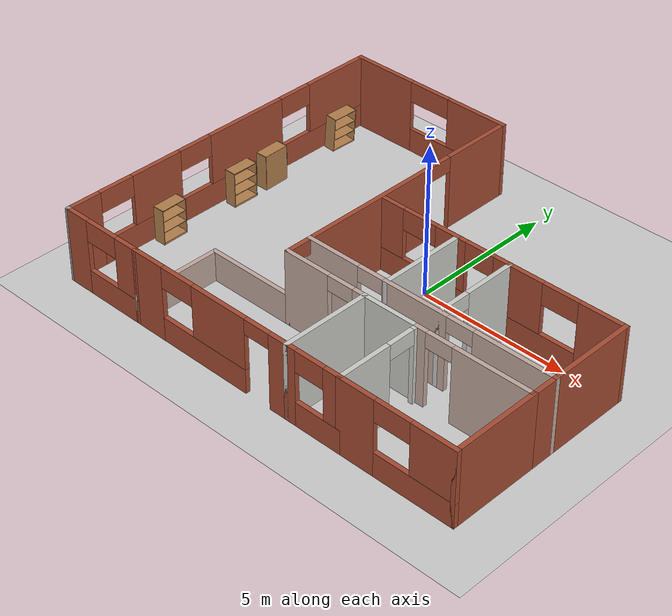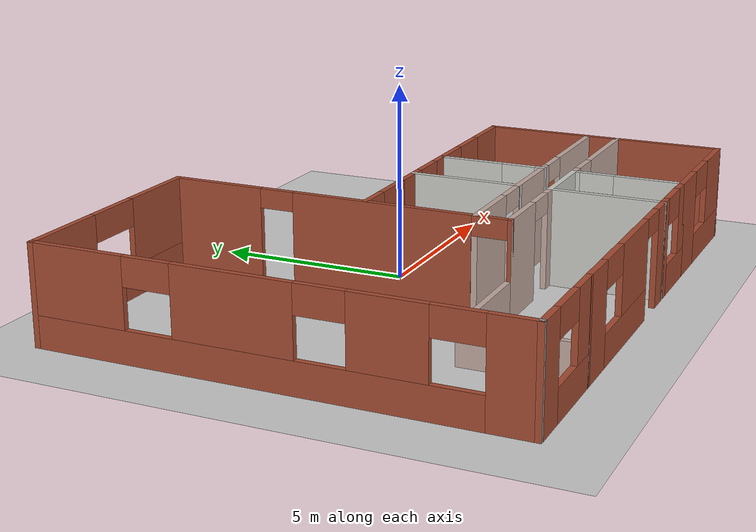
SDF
<sdf version="1.6">
 <world name="default">
  <plugin name="welcome" filename="libwelcome.so"/>
  <light name="sun" type="directional">
   <pose>0 0 10 0 -0 0</pose>
   <diffuse>0.8 0.8 0.8 1</diffuse>
   <specular>0.2 0.2 0.2 1</specular>
   <attenuation>
    <range>1000</range>
    <constant>0.9</constant>
    <linear>0.01</linear>
    <quadratic>0.001</quadratic>
   </attenuation>
   <direction>-0.5 0.1 -0.9</direction>
  </light>
  <model name="ground_plane">
   <static>1</static>
   <link name="link">
    <collision name="collision">
     <geometry><plane><normal>0 0 1</normal><size>100 100</size></plane></geometry>
     <surface><friction><ode><mu>100</mu><mu2>50</mu2></ode></friction></surface>
    </collision>
    <visual name="visual">
     <cast_shadows>0</cast_shadows>
     <geometry><plane><normal>0 0 1</normal><size>100 100</size></plane></geometry>
     <material>
      <script><uri>file://media/materials/scripts/gazebo.material</uri><name>Gazebo/Grey</name></script>
     </material>
    </visual>
   </link>
  </model>
  <gravity>0 0 -9.8</gravity>
  <magnetic_field>6e-06 2.3e-05 -4.2e-05</magnetic_field>
  <atmosphere type="adiabatic"/>
  <physics name="default_physics" default="0" type="ode">
   <max_step_size>0.001</max_step_size>
   <real_time_factor>1</real_time_factor>
   <real_time_update_rate>1000</real_time_update_rate>
  </physics>
  <scene><ambient>0.4 0.4 0.4 1</ambient><background>0.7 0.7 0.7 1</background><shadows>1</shadows></scene>
  <spherical_coordinates>
   <surface_model>EARTH_WGS84</surface_model>
   <latitude_deg>0</latitude_deg>
   <longitude_deg>0</longitude_deg>
   <elevation>0</elevation>
   <heading_deg>0</heading_deg>
  </spherical_coordinates>
  <model name="robot">
   <link name="link_0">
    <pose>0 0 -1e-05 0 -0 0</pose>
    <inertial>
     <mass>1</mass>
     <inertia>
      <ixx>0.166667</ixx>
      <ixy>0</ixy>
      <ixz>0</ixz>
      <iyy>0.166667</iyy>
      <iyz>0</iyz>
      <izz>0.166667</izz>
     </inertia>
    </inertial>
    <visual name="visual">
     <geometry><box><size>0.3 0.3 0.03</size></box></geometry>
     <material>
      <lighting>1</lighting>
      <script><uri>file://media/materials/scripts/gazebo.material</uri><name>Gazebo/Grey</name></script>
      <ambient>0.3 0.3 0.3 1</ambient>
      <diffuse>0.7 0.7 0.7 1</diffuse>
      <specular>0.01 0.01 0.01 1</specular>
      <emissive>0 0 0 1</emissive>
      <shader type="vertex"><normal_map>__default__</normal_map></shader>
     </material>
    </visual>
    <collision name="collision">
     <geometry><box><size>0.3 0.3 0.03</size></box></geometry>
     <surface>
      <friction>
       <ode><mu>1</mu><mu2>1</mu2><fdir1>0 0 0</fdir1><slip1>0</slip1><slip2>0</slip2></ode>
       <torsional>
        <coefficient>1</coefficient>
        <patch_radius>0</patch_radius>
        <surface_radius>0</surface_radius>
        <use_patch_radius>1</use_patch_radius>
        <ode><slip>0</slip></ode>
       </torsional>
      </friction>
      <bounce><restitution_coefficient>0</restitution_coefficient><threshold>1e+06</threshold></bounce>
      <contact>
       <collide_without_contact>0</collide_without_contact>
       <collide_without_contact_bitmask>1</collide_without_contact_bitmask>
       <collide_bitmask>1</collide_bitmask>
       <ode>
        <soft_cfm>0</soft_cfm>
        <soft_erp>0.2</soft_erp>
        <kp>1e+13</kp>
        <kd>1</kd>
        <max_vel>0.01</max_vel>
        <min_depth>0</min_depth>
       </ode>
       <bullet>
        <split_impulse>1</split_impulse>
        <split_impulse_penetration_threshold>-0.01</split_impulse_penetration_threshold>
        <soft_cfm>0</soft_cfm>
        <soft_erp>0.2</soft_erp>
        <kp>1e+13</kp>
        <kd>1</kd>
       </bullet>
      </contact>
     </surface>
    </collision>
   </link>
   <link name="link_1">
    <pose>0.09 -0.165006 2e-06 1.5707 -0 0</pose>
    <inertial>
     <mass>1</mass>
     <inertia><ixx>0.145833</ixx><ixy>0</ixy><ixz>0</ixz><iyy>0.145833</iyy><iyz>0</iyz><izz>0.125</izz></inertia>
    </inertial>
    <visual name="visual">
     <geometry><cylinder><radius>0.06</radius><length>0.03</length></cylinder></geometry>
     <material>
      <lighting>1</lighting>
      <script><uri>file://media/materials/scripts/gazebo.material</uri><name>Gazebo/Grey</name></script>
      <ambient>0.3 0.3 0.3 1</ambient>
      <diffuse>0.7 0.7 0.7 1</diffuse>
      <specular>0.01 0.01 0.01 1</specular>
      <emissive>0 0 0 1</emissive>
      <shader type="vertex"><normal_map>__default__</normal_map></shader>
     </material>
    </visual>
    <collision name="collision">
     <geometry><cylinder><radius>0.06</radius><length>0.03</length></cylinder></geometry>
     <surface>
      <friction>
       <ode><mu>1</mu><mu2>1</mu2><fdir1>0 0 0</fdir1><slip1>0</slip1><slip2>0</slip2></ode>
       <torsional>
        <coefficient>1</coefficient>
        <patch_radius>0</patch_radius>
        <surface_radius>0</surface_radius>
        <use_patch_radius>1</use_patch_radius>
        <ode><slip>0</slip></ode>
       </torsional>
      </friction>
      <bounce><restitution_coefficient>0</restitution_coefficient><threshold>1e+06</threshold></bounce>
      <contact>
       <collide_without_contact>0</collide_without_contact>
       <collide_without_contact_bitmask>1</collide_without_contact_bitmask>
       <collide_bitmask>1</collide_bitmask>
       <ode>
        <soft_cfm>0</soft_cfm>
        <soft_erp>0.2</soft_erp>
        <kp>1e+13</kp>
        <kd>1</kd>
        <max_vel>0.01</max_vel>
        <min_depth>0</min_depth>
       </ode>
       <bullet>
        <split_impulse>1</split_impulse>
        <split_impulse_penetration_threshold>-0.01</split_impulse_penetration_threshold>
        <soft_cfm>0</soft_cfm>
        <soft_erp>0.2</soft_erp>
        <kp>1e+13</kp>
        <kd>1</kd>
       </bullet>
      </contact>
     </surface>
    </collision>
   </link>
   <link name="link_1_clone">
    <pose>-0.09 -0.165006 2e-06 1.5707 -0 0</pose>
    <inertial>
     <mass>1</mass>
     <inertia><ixx>0.145833</ixx><ixy>0</ixy><ixz>0</ixz><iyy>0.145833</iyy><iyz>0</iyz><izz>0.125</izz></inertia>
    </inertial>
    <visual name="visual">
     <geometry><cylinder><radius>0.06</radius><length>0.03</length></cylinder></geometry>
     <material>
      <lighting>1</lighting>
      <script><uri>file://media/materials/scripts/gazebo.material</uri><name>Gazebo/Grey</name></script>
      <ambient>0.3 0.3 0.3 1</ambient>
      <diffuse>0.7 0.7 0.7 1</diffuse>
      <specular>0.01 0.01 0.01 1</specular>
      <emissive>0 0 0 1</emissive>
      <shader type="vertex"><normal_map>__default__</normal_map></shader>
     </material>
    </visual>
    <collision name="collision">
     <geometry><cylinder><radius>0.06</radius><length>0.03</length></cylinder></geometry>
     <surface>
      <friction>
       <ode><mu>1</mu><mu2>1</mu2><fdir1>0 0 0</fdir1><slip1>0</slip1><slip2>0</slip2></ode>
       <torsional>
        <coefficient>1</coefficient>
        <patch_radius>0</patch_radius>
        <surface_radius>0</surface_radius>
        <use_patch_radius>1</use_patch_radius>
        <ode><slip>0</slip></ode>
       </torsional>
      </friction>
      <bounce><restitution_coefficient>0</restitution_coefficient><threshold>1e+06</threshold></bounce>
      <contact>
       <collide_without_contact>0</collide_without_contact>
       <collide_without_contact_bitmask>1</collide_without_contact_bitmask>
       <collide_bitmask>1</collide_bitmask>
       <ode>
        <soft_cfm>0</soft_cfm>
        <soft_erp>0.2</soft_erp>
        <kp>1e+13</kp>
        <kd>1</kd>
        <max_vel>0.01</max_vel>
        <min_depth>0</min_depth>
       </ode>
       <bullet>
        <split_impulse>1</split_impulse>
        <split_impulse_penetration_threshold>-0.01</split_impulse_penetration_threshold>
        <soft_cfm>0</soft_cfm>
        <soft_erp>0.2</soft_erp>
        <kp>1e+13</kp>
        <kd>1</kd>
       </bullet>
      </contact>
     </surface>
    </collision>
   </link>
   <link name="link_1_clone_0">
    <pose>0.09 0.165006 2e-06 1.5707 -0 0</pose>
    <inertial>
     <mass>1</mass>
     <inertia><ixx>0.145833</ixx><ixy>0</ixy><ixz>0</ixz><iyy>0.145833</iyy><iyz>0</iyz><izz>0.125</izz></inertia>
    </inertial>
    <visual name="visual">
     <geometry><cylinder><radius>0.06</radius><length>0.03</length></cylinder></geometry>
     <material>
      <lighting>1</lighting>
      <script><uri>file://media/materials/scripts/gazebo.material</uri><name>Gazebo/Grey</name></script>
      <ambient>0.3 0.3 0.3 1</ambient>
      <diffuse>0.7 0.7 0.7 1</diffuse>
      <specular>0.01 0.01 0.01 1</specular>
      <emissive>0 0 0 1</emissive>
      <shader type="vertex"><normal_map>__default__</normal_map></shader>
     </material>
    </visual>
    <collision name="collision">
     <geometry><cylinder><radius>0.06</radius><length>0.03</length></cylinder></geometry>
     <surface>
      <friction>
       <ode><mu>1</mu><mu2>1</mu2><fdir1>0 0 0</fdir1><slip1>0</slip1><slip2>0</slip2></ode>
       <torsional>
        <coefficient>1</coefficient>
        <patch_radius>0</patch_radius>
        <surface_radius>0</surface_radius>
        <use_patch_radius>1</use_patch_radius>
        <ode><slip>0</slip></ode>
       </torsional>
      </friction>
      <bounce><restitution_coefficient>0</restitution_coefficient><threshold>1e+06</threshold></bounce>
      <contact>
       <collide_without_contact>0</collide_without_contact>
       <collide_without_contact_bitmask>1</collide_without_contact_bitmask>
       <collide_bitmask>1</collide_bitmask>
       <ode>
        <soft_cfm>0</soft_cfm>
        <soft_erp>0.2</soft_erp>
        <kp>1e+13</kp>
        <kd>1</kd>
        <max_vel>0.01</max_vel>
        <min_depth>0</min_depth>
       </ode>
       <bullet>
        <split_impulse>1</split_impulse>
        <split_impulse_penetration_threshold>-0.01</split_impulse_penetration_threshold>
        <soft_cfm>0</soft_cfm>
        <soft_erp>0.2</soft_erp>
        <kp>1e+13</kp>
        <kd>1</kd>
       </bullet>
      </contact>
     </surface>
    </collision>
   </link>
   <link name="link_1_clone_1">
    <pose>-0.09 0.165006 2e-06 1.5707 -0 0</pose>
    <inertial>
     <mass>1</mass>
     <inertia><ixx>0.145833</ixx><ixy>0</ixy><ixz>0</ixz><iyy>0.145833</iyy><iyz>0</iyz><izz>0.125</izz></inertia>
    </inertial>
    <visual name="visual">
     <geometry><cylinder><radius>0.06</radius><length>0.03</length></cylinder></geometry>
     <material>
      <lighting>1</lighting>
      <script><uri>file://media/materials/scripts/gazebo.material</uri><name>Gazebo/Grey</name></script>
      <ambient>0.3 0.3 0.3 1</ambient>
      <diffuse>0.7 0.7 0.7 1</diffuse>
      <specular>0.01 0.01 0.01 1</specular>
      <emissive>0 0 0 1</emissive>
      <shader type="vertex"><normal_map>__default__</normal_map></shader>
     </material>
    </visual>
    <collision name="collision">
     <geometry><cylinder><radius>0.06</radius><length>0.03</length></cylinder></geometry>
     <surface>
      <friction>
       <ode><mu>1</mu><mu2>1</mu2><fdir1>0 0 0</fdir1><slip1>0</slip1><slip2>0</slip2></ode>
       <torsional>
        <coefficient>1</coefficient>
        <patch_radius>0</patch_radius>
        <surface_radius>0</surface_radius>
        <use_patch_radius>1</use_patch_radius>
        <ode><slip>0</slip></ode>
       </torsional>
      </friction>
      <bounce><restitution_coefficient>0</restitution_coefficient><threshold>1e+06</threshold></bounce>
      <contact>
       <collide_without_contact>0</collide_without_contact>
       <collide_without_contact_bitmask>1</collide_without_contact_bitmask>
       <collide_bitmask>1</collide_bitmask>
       <ode>
        <soft_cfm>0</soft_cfm>
        <soft_erp>0.2</soft_erp>
        <kp>1e+13</kp>
        <kd>1</kd>
        <max_vel>0.01</max_vel>
        <min_depth>0</min_depth>
       </ode>
       <bullet>
        <split_impulse>1</split_impulse>
        <split_impulse_penetration_threshold>-0.01</split_impulse_penetration_threshold>
        <soft_cfm>0</soft_cfm>
        <soft_erp>0.2</soft_erp>
        <kp>1e+13</kp>
        <kd>1</kd>
       </bullet>
      </contact>
     </surface>
    </collision>
   </link>
   <joint name="link_0_JOINT_0" type="revolute">
    <parent>link_0</parent>
    <child>link_1</child>
    <axis>
     <xyz>0 0 1</xyz>
     <use_parent_model_frame>0</use_parent_model_frame>
     <limit>
      <lower>-1.79769e+308</lower>
      <upper>1.79769e+308</upper>
      <effort>-1</effort>
      <velocity>-1</velocity>
     </limit>
     <dynamics>
      <spring_reference>0</spring_reference>
      <spring_stiffness>0</spring_stiffness>
      <damping>0</damping>
     </dynamics>
    </axis>
    <physics>
     <ode><limit><cfm>0</cfm><erp>0.2</erp></limit><suspension><cfm>0</cfm><erp>0.2</erp></suspension></ode>
    </physics>
   </joint>
   <joint name="link_0_JOINT_1" type="revolute">
    <parent>link_0</parent>
    <child>link_1_clone</child>
    <axis>
     <xyz>0 0 1</xyz>
     <use_parent_model_frame>0</use_parent_model_frame>
     <limit>
      <lower>-1.79769e+308</lower>
      <upper>1.79769e+308</upper>
      <effort>-1</effort>
      <velocity>-1</velocity>
     </limit>
     <dynamics>
      <spring_reference>0</spring_reference>
      <spring_stiffness>0</spring_stiffness>
      <damping>0</damping>
     </dynamics>
    </axis>
    <physics>
     <ode><limit><cfm>0</cfm><erp>0.2</erp></limit><suspension><cfm>0</cfm><erp>0.2</erp></suspension></ode>
    </physics>
   </joint>
   <joint name="link_0_JOINT_2" type="revolute">
    <parent>link_0</parent>
    <child>link_1_clone_0</child>
    <axis>
     <xyz>0 0 1</xyz>
     <use_parent_model_frame>0</use_parent_model_frame>
     <limit>
      <lower>-1.79769e+308</lower>
      <upper>1.79769e+308</upper>
      <effort>-1</effort>
      <velocity>-1</velocity>
     </limit>
     <dynamics>
      <spring_reference>0</spring_reference>
      <spring_stiffness>0</spring_stiffness>
      <damping>0</damping>
     </dynamics>
    </axis>
    <physics>
     <ode><limit><cfm>0</cfm><erp>0.2</erp></limit><suspension><cfm>0</cfm><erp>0.2</erp></suspension></ode>
    </physics>
   </joint>
   <joint name="link_0_JOINT_3" type="revolute">
    <parent>link_0</parent>
    <child>link_1_clone_1</child>
    <axis>
     <xyz>0 0 1</xyz>
     <use_parent_model_frame>0</use_parent_model_frame>
     <limit>
      <lower>-1.79769e+308</lower>
      <upper>1.79769e+308</upper>
      <effort>-1</effort>
      <velocity>-1</velocity>
     </limit>
     <dynamics>
      <spring_reference>0</spring_reference>
      <spring_stiffness>0</spring_stiffness>
      <damping>0</damping>
     </dynamics>
    </axis>
    <physics>
     <ode><limit><cfm>0</cfm><erp>0.2</erp></limit><suspension><cfm>0</cfm><erp>0.2</erp></suspension></ode>
    </physics>
   </joint>
   <static>0</static>
   <pose>-2.65526 -0.348359 0.059998 2e-06 1.5e-05 0.105774</pose>
  </model>
  <model name="robot_0">
   <link name="link_0">
    <pose>0 0 -1e-05 0 -0 0</pose>
    <inertial>
     <mass>1</mass>
     <inertia>
      <ixx>0.166667</ixx>
      <ixy>0</ixy>
      <ixz>0</ixz>
      <iyy>0.166667</iyy>
      <iyz>0</iyz>
      <izz>0.166667</izz>
     </inertia>
    </inertial>
    <visual name="visual">
     <geometry><box><size>0.3 0.3 0.03</size></box></geometry>
     <material>
      <lighting>1</lighting>
      <script><uri>file://media/materials/scripts/gazebo.material</uri><name>Gazebo/Grey</name></script>
      <ambient>0.3 0.3 0.3 1</ambient>
      <diffuse>0.7 0.7 0.7 1</diffuse>
      <specular>0.01 0.01 0.01 1</specular>
      <emissive>0 0 0 1</emissive>
      <shader type="vertex"><normal_map>__default__</normal_map></shader>
     </material>
    </visual>
    <collision name="collision">
     <geometry><box><size>0.3 0.3 0.03</size></box></geometry>
     <surface>
      <friction>
       <ode><mu>1</mu><mu2>1</mu2><fdir1>0 0 0</fdir1><slip1>0</slip1><slip2>0</slip2></ode>
       <torsional>
        <coefficient>1</coefficient>
        <patch_radius>0</patch_radius>
        <surface_radius>0</surface_radius>
        <use_patch_radius>1</use_patch_radius>
        <ode><slip>0</slip></ode>
       </torsional>
      </friction>
      <bounce><restitution_coefficient>0</restitution_coefficient><threshold>1e+06</threshold></bounce>
      <contact>
       <collide_without_contact>0</collide_without_contact>
       <collide_without_contact_bitmask>1</collide_without_contact_bitmask>
       <collide_bitmask>1</collide_bitmask>
       <ode>
        <soft_cfm>0</soft_cfm>
        <soft_erp>0.2</soft_erp>
        <kp>1e+13</kp>
        <kd>1</kd>
        <max_vel>0.01</max_vel>
        <min_depth>0</min_depth>
       </ode>
       <bullet>
        <split_impulse>1</split_impulse>
        <split_impulse_penetration_threshold>-0.01</split_impulse_penetration_threshold>
        <soft_cfm>0</soft_cfm>
        <soft_erp>0.2</soft_erp>
        <kp>1e+13</kp>
        <kd>1</kd>
       </bullet>
      </contact>
     </surface>
    </collision>
   </link>
   <link name="link_1">
    <pose>0.09 -0.165006 2e-06 1.5707 -0 0</pose>
    <inertial>
     <mass>1</mass>
     <inertia><ixx>0.145833</ixx><ixy>0</ixy><ixz>0</ixz><iyy>0.145833</iyy><iyz>0</iyz><izz>0.125</izz></inertia>
    </inertial>
    <visual name="visual">
     <geometry><cylinder><radius>0.06</radius><length>0.03</length></cylinder></geometry>
     <material>
      <lighting>1</lighting>
      <script><uri>file://media/materials/scripts/gazebo.material</uri><name>Gazebo/Grey</name></script>
      <ambient>0.3 0.3 0.3 1</ambient>
      <diffuse>0.7 0.7 0.7 1</diffuse>
      <specular>0.01 0.01 0.01 1</specular>
      <emissive>0 0 0 1</emissive>
      <shader type="vertex"><normal_map>__default__</normal_map></shader>
     </material>
    </visual>
    <collision name="collision">
     <geometry><cylinder><radius>0.06</radius><length>0.03</length></cylinder></geometry>
     <surface>
      <friction>
       <ode><mu>1</mu><mu2>1</mu2><fdir1>0 0 0</fdir1><slip1>0</slip1><slip2>0</slip2></ode>
       <torsional>
        <coefficient>1</coefficient>
        <patch_radius>0</patch_radius>
        <surface_radius>0</surface_radius>
        <use_patch_radius>1</use_patch_radius>
        <ode><slip>0</slip></ode>
       </torsional>
      </friction>
      <bounce><restitution_coefficient>0</restitution_coefficient><threshold>1e+06</threshold></bounce>
      <contact>
       <collide_without_contact>0</collide_without_contact>
       <collide_without_contact_bitmask>1</collide_without_contact_bitmask>
       <collide_bitmask>1</collide_bitmask>
       <ode>
        <soft_cfm>0</soft_cfm>
        <soft_erp>0.2</soft_erp>
        <kp>1e+13</kp>
        <kd>1</kd>
        <max_vel>0.01</max_vel>
        <min_depth>0</min_depth>
       </ode>
       <bullet>
        <split_impulse>1</split_impulse>
        <split_impulse_penetration_threshold>-0.01</split_impulse_penetration_threshold>
        <soft_cfm>0</soft_cfm>
        <soft_erp>0.2</soft_erp>
        <kp>1e+13</kp>
        <kd>1</kd>
       </bullet>
      </contact>
     </surface>
    </collision>
   </link>
   <link name="link_1_clone">
    <pose>-0.09 -0.165006 2e-06 1.5707 -0 0</pose>
    <inertial>
     <mass>1</mass>
     <inertia><ixx>0.145833</ixx><ixy>0</ixy><ixz>0</ixz><iyy>0.145833</iyy><iyz>0</iyz><izz>0.125</izz></inertia>
    </inertial>
    <visual name="visual">
     <geometry><cylinder><radius>0.06</radius><length>0.03</length></cylinder></geometry>
     <material>
      <lighting>1</lighting>
      <script><uri>file://media/materials/scripts/gazebo.material</uri><name>Gazebo/Grey</name></script>
      <ambient>0.3 0.3 0.3 1</ambient>
      <diffuse>0.7 0.7 0.7 1</diffuse>
      <specular>0.01 0.01 0.01 1</specular>
      <emissive>0 0 0 1</emissive>
      <shader type="vertex"><normal_map>__default__</normal_map></shader>
     </material>
    </visual>
    <collision name="collision">
     <geometry><cylinder><radius>0.06</radius><length>0.03</length></cylinder></geometry>
     <surface>
      <friction>
       <ode><mu>1</mu><mu2>1</mu2><fdir1>0 0 0</fdir1><slip1>0</slip1><slip2>0</slip2></ode>
       <torsional>
        <coefficient>1</coefficient>
        <patch_radius>0</patch_radius>
        <surface_radius>0</surface_radius>
        <use_patch_radius>1</use_patch_radius>
        <ode><slip>0</slip></ode>
       </torsional>
      </friction>
      <bounce><restitution_coefficient>0</restitution_coefficient><threshold>1e+06</threshold></bounce>
      <contact>
       <collide_without_contact>0</collide_without_contact>
       <collide_without_contact_bitmask>1</collide_without_contact_bitmask>
       <collide_bitmask>1</collide_bitmask>
       <ode>
        <soft_cfm>0</soft_cfm>
        <soft_erp>0.2</soft_erp>
        <kp>1e+13</kp>
        <kd>1</kd>
        <max_vel>0.01</max_vel>
        <min_depth>0</min_depth>
       </ode>
       <bullet>
        <split_impulse>1</split_impulse>
        <split_impulse_penetration_threshold>-0.01</split_impulse_penetration_threshold>
        <soft_cfm>0</soft_cfm>
        <soft_erp>0.2</soft_erp>
        <kp>1e+13</kp>
        <kd>1</kd>
       </bullet>
      </contact>
     </surface>
    </collision>
   </link>
   <link name="link_1_clone_0">
    <pose>0.09 0.165006 2e-06 1.5707 -0 0</pose>
    <inertial>
     <mass>1</mass>
     <inertia><ixx>0.145833</ixx><ixy>0</ixy><ixz>0</ixz><iyy>0.145833</iyy><iyz>0</iyz><izz>0.125</izz></inertia>
    </inertial>
    <visual name="visual">
     <geometry><cylinder><radius>0.06</radius><length>0.03</length></cylinder></geometry>
     <material>
      <lighting>1</lighting>
      <script><uri>file://media/materials/scripts/gazebo.material</uri><name>Gazebo/Grey</name></script>
      <ambient>0.3 0.3 0.3 1</ambient>
      <diffuse>0.7 0.7 0.7 1</diffuse>
      <specular>0.01 0.01 0.01 1</specular>
      <emissive>0 0 0 1</emissive>
      <shader type="vertex"><normal_map>__default__</normal_map></shader>
     </material>
    </visual>
    <collision name="collision">
     <geometry><cylinder><radius>0.06</radius><length>0.03</length></cylinder></geometry>
     <surface>
      <friction>
       <ode><mu>1</mu><mu2>1</mu2><fdir1>0 0 0</fdir1><slip1>0</slip1><slip2>0</slip2></ode>
       <torsional>
        <coefficient>1</coefficient>
        <patch_radius>0</patch_radius>
        <surface_radius>0</surface_radius>
        <use_patch_radius>1</use_patch_radius>
        <ode><slip>0</slip></ode>
       </torsional>
      </friction>
      <bounce><restitution_coefficient>0</restitution_coefficient><threshold>1e+06</threshold></bounce>
      <contact>
       <collide_without_contact>0</collide_without_contact>
       <collide_without_contact_bitmask>1</collide_without_contact_bitmask>
       <collide_bitmask>1</collide_bitmask>
       <ode>
        <soft_cfm>0</soft_cfm>
        <soft_erp>0.2</soft_erp>
        <kp>1e+13</kp>
        <kd>1</kd>
        <max_vel>0.01</max_vel>
        <min_depth>0</min_depth>
       </ode>
       <bullet>
        <split_impulse>1</split_impulse>
        <split_impulse_penetration_threshold>-0.01</split_impulse_penetration_threshold>
        <soft_cfm>0</soft_cfm>
        <soft_erp>0.2</soft_erp>
        <kp>1e+13</kp>
        <kd>1</kd>
       </bullet>
      </contact>
     </surface>
    </collision>
   </link>
   <link name="link_1_clone_1">
    <pose>-0.09 0.165006 2e-06 1.5707 -0 0</pose>
    <inertial>
     <mass>1</mass>
     <inertia><ixx>0.145833</ixx><ixy>0</ixy><ixz>0</ixz><iyy>0.145833</iyy><iyz>0</iyz><izz>0.125</izz></inertia>
    </inertial>
    <visual name="visual">
     <geometry><cylinder><radius>0.06</radius><length>0.03</length></cylinder></geometry>
     <material>
      <lighting>1</lighting>
      <script><uri>file://media/materials/scripts/gazebo.material</uri><name>Gazebo/Grey</name></script>
      <ambient>0.3 0.3 0.3 1</ambient>
      <diffuse>0.7 0.7 0.7 1</diffuse>
      <specular>0.01 0.01 0.01 1</specular>
      <emissive>0 0 0 1</emissive>
      <shader type="vertex"><normal_map>__default__</normal_map></shader>
     </material>
    </visual>
    <collision name="collision">
     <geometry><cylinder><radius>0.06</radius><length>0.03</length></cylinder></geometry>
     <surface>
      <friction>
       <ode><mu>1</mu><mu2>1</mu2><fdir1>0 0 0</fdir1><slip1>0</slip1><slip2>0</slip2></ode>
       <torsional>
        <coefficient>1</coefficient>
        <patch_radius>0</patch_radius>
        <surface_radius>0</surface_radius>
        <use_patch_radius>1</use_patch_radius>
        <ode><slip>0</slip></ode>
       </torsional>
      </friction>
      <bounce><restitution_coefficient>0</restitution_coefficient><threshold>1e+06</threshold></bounce>
      <contact>
       <collide_without_contact>0</collide_without_contact>
       <collide_without_contact_bitmask>1</collide_without_contact_bitmask>
       <collide_bitmask>1</collide_bitmask>
       <ode>
        <soft_cfm>0</soft_cfm>
        <soft_erp>0.2</soft_erp>
        <kp>1e+13</kp>
        <kd>1</kd>
        <max_vel>0.01</max_vel>
        <min_depth>0</min_depth>
       </ode>
       <bullet>
        <split_impulse>1</split_impulse>
        <split_impulse_penetration_threshold>-0.01</split_impulse_penetration_threshold>
        <soft_cfm>0</soft_cfm>
        <soft_erp>0.2</soft_erp>
        <kp>1e+13</kp>
        <kd>1</kd>
       </bullet>
      </contact>
     </surface>
    </collision>
   </link>
   <joint name="link_0_JOINT_0" type="revolute">
    <parent>link_0</parent>
    <child>link_1</child>
    <axis>
     <xyz>0 0 1</xyz>
     <use_parent_model_frame>0</use_parent_model_frame>
     <limit>
      <lower>-1.79769e+308</lower>
      <upper>1.79769e+308</upper>
      <effort>-1</effort>
      <velocity>-1</velocity>
     </limit>
     <dynamics>
      <spring_reference>0</spring_reference>
      <spring_stiffness>0</spring_stiffness>
      <damping>0</damping>
     </dynamics>
    </axis>
    <physics>
     <ode><limit><cfm>0</cfm><erp>0.2</erp></limit><suspension><cfm>0</cfm><erp>0.2</erp></suspension></ode>
    </physics>
   </joint>
   <joint name="link_0_JOINT_1" type="revolute">
    <parent>link_0</parent>
    <child>link_1_clone</child>
    <axis>
     <xyz>0 0 1</xyz>
     <use_parent_model_frame>0</use_parent_model_frame>
     <limit>
      <lower>-1.79769e+308</lower>
      <upper>1.79769e+308</upper>
      <effort>-1</effort>
      <velocity>-1</velocity>
     </limit>
     <dynamics>
      <spring_reference>0</spring_reference>
      <spring_stiffness>0</spring_stiffness>
      <damping>0</damping>
     </dynamics>
    </axis>
    <physics>
     <ode><limit><cfm>0</cfm><erp>0.2</erp></limit><suspension><cfm>0</cfm><erp>0.2</erp></suspension></ode>
    </physics>
   </joint>
   <joint name="link_0_JOINT_2" type="revolute">
    <parent>link_0</parent>
    <child>link_1_clone_0</child>
    <axis>
     <xyz>0 0 1</xyz>
     <use_parent_model_frame>0</use_parent_model_frame>
     <limit>
      <lower>-1.79769e+308</lower>
      <upper>1.79769e+308</upper>
      <effort>-1</effort>
      <velocity>-1</velocity>
     </limit>
     <dynamics>
      <spring_reference>0</spring_reference>
      <spring_stiffness>0</spring_stiffness>
      <damping>0</damping>
     </dynamics>
    </axis>
    <physics>
     <ode><limit><cfm>0</cfm><erp>0.2</erp></limit><suspension><cfm>0</cfm><erp>0.2</erp></suspension></ode>
    </physics>
   </joint>
   <joint name="link_0_JOINT_3" type="revolute">
    <parent>link_0</parent>
    <child>link_1_clone_1</child>
    <axis>
     <xyz>0 0 1</xyz>
     <use_parent_model_frame>0</use_parent_model_frame>
     <limit>
      <lower>-1.79769e+308</lower>
      <upper>1.79769e+308</upper>
      <effort>-1</effort>
      <velocity>-1</velocity>
     </limit>
     <dynamics>
      <spring_reference>0</spring_reference>
      <spring_stiffness>0</spring_stiffness>
      <damping>0</damping>
     </dynamics>
    </axis>
    <physics>
     <ode><limit><cfm>0</cfm><erp>0.2</erp></limit><suspension><cfm>0</cfm><erp>0.2</erp></suspension></ode>
    </physics>
   </joint>
   <static>0</static>
   <pose>0.470561 -5.00667 0.059998 6e-06 -9e-06 0.093049</pose>
  </model>
  <model name="mybuilding">
   <pose>-0.45888 -0.542474 0 0 -0 0</pose>
   <link name="Wall_0">
    <pose>-7.19982 0.000123 0 0 -0 1.5708</pose>
    <visual name="Wall_0_Visual_0">
     <pose>-5.41232 0 1.25 0 -0 0</pose>
     <geometry><box><size>1.17536 0.15 2.5</size></box></geometry>
     <material>
      <script><uri>file://media/materials/scripts/gazebo.material</uri><name>Gazebo/Bricks</name></script>
      <ambient>1 1 1 1</ambient>
     </material>
     <meta><layer>0</layer></meta>
    </visual>
    <collision name="Wall_0_Collision_0">
     <geometry><box><size>1.17536 0.15 2.5</size></box></geometry>
     <pose>-5.41232 0 1.25 0 -0 0</pose>
    </collision>
    <visual name="Wall_0_Visual_1">
     <pose>0.587679 0 0.4 0 -0 0</pose>
     <geometry><box><size>10.8246 0.15 0.8</size></box></geometry>
     <material>
      <script><uri>file://media/materials/scripts/gazebo.material</uri><name>Gazebo/Bricks</name></script>
      <ambient>1 1 1 1</ambient>
     </material>
     <meta><layer>0</layer></meta>
    </visual>
    <collision name="Wall_0_Collision_1">
     <geometry><box><size>10.8246 0.15 0.8</size></box></geometry>
     <pose>0.587679 0 0.4 0 -0 0</pose>
    </collision>
    <visual name="Wall_0_Visual_2">
     <pose>-2.71261 0 1.65 0 -0 0</pose>
     <geometry><box><size>1.82405 0.15 1.7</size></box></geometry>
     <material>
      <script><uri>file://media/materials/scripts/gazebo.material</uri><name>Gazebo/Bricks</name></script>
      <ambient>1 1 1 1</ambient>
     </material>
     <meta><layer>0</layer></meta>
    </visual>
    <collision name="Wall_0_Collision_2">
     <geometry><box><size>1.82405 0.15 1.7</size></box></geometry>
     <pose>-2.71261 0 1.65 0 -0 0</pose>
    </collision>
    <visual name="Wall_0_Visual_3">
     <pose>0.869727 0 1.65 0 -0 0</pose>
     <geometry><box><size>2.94063 0.15 1.7</size></box></geometry>
     <material>
      <script><uri>file://media/materials/scripts/gazebo.material</uri><name>Gazebo/Bricks</name></script>
      <ambient>1 1 1 1</ambient>
     </material>
     <meta><layer>0</layer></meta>
    </visual>
    <collision name="Wall_0_Collision_3">
     <geometry><box><size>2.94063 0.15 1.7</size></box></geometry>
     <pose>0.869727 0 1.65 0 -0 0</pose>
    </collision>
    <visual name="Wall_0_Visual_4">
     <pose>4.77002 0 1.65 0 -0 0</pose>
     <geometry><box><size>2.45996 0.15 1.7</size></box></geometry>
     <material>
      <script><uri>file://media/materials/scripts/gazebo.material</uri><name>Gazebo/Bricks</name></script>
      <ambient>1 1 1 1</ambient>
     </material>
     <meta><layer>0</layer></meta>
    </visual>
    <collision name="Wall_0_Collision_4">
     <geometry><box><size>2.45996 0.15 1.7</size></box></geometry>
     <pose>4.77002 0 1.65 0 -0 0</pose>
    </collision>
    <visual name="Wall_0_Visual_5">
     <pose>-4.22464 0 2.15 0 -0 0</pose>
     <geometry><box><size>1.2 0.15 0.7</size></box></geometry>
     <material>
      <script><uri>file://media/materials/scripts/gazebo.material</uri><name>Gazebo/Bricks</name></script>
      <ambient>1 1 1 1</ambient>
     </material>
     <meta><layer>0</layer></meta>
    </visual>
    <collision name="Wall_0_Collision_5">
     <geometry><box><size>1.2 0.15 0.7</size></box></geometry>
     <pose>-4.22464 0 2.15 0 -0 0</pose>
    </collision>
    <visual name="Wall_0_Visual_6">
     <pose>-1.20059 0 2.15 0 -0 0</pose>
     <geometry><box><size>1.2 0.15 0.7</size></box></geometry>
     <material>
      <script><uri>file://media/materials/scripts/gazebo.material</uri><name>Gazebo/Bricks</name></script>
      <ambient>1 1 1 1</ambient>
     </material>
     <meta><layer>0</layer></meta>
    </visual>
    <collision name="Wall_0_Collision_6">
     <geometry><box><size>1.2 0.15 0.7</size></box></geometry>
     <pose>-1.20059 0 2.15 0 -0 0</pose>
    </collision>
    <visual name="Wall_0_Visual_7">
     <pose>2.94004 0 2.15 0 -0 0</pose>
     <geometry><box><size>1.2 0.15 0.7</size></box></geometry>
     <material>
      <script><uri>file://media/materials/scripts/gazebo.material</uri><name>Gazebo/Bricks</name></script>
      <ambient>1 1 1 1</ambient>
     </material>
     <meta><layer>0</layer></meta>
    </visual>
    <collision name="Wall_0_Collision_7">
     <geometry><box><size>1.2 0.15 0.7</size></box></geometry>
     <pose>2.94004 0 2.15 0 -0 0</pose>
    </collision>
   </link>
   <link name="Wall_10">
    <collision name="Wall_10_Collision">
     <geometry><box><size>3 0.15 1</size></box></geometry>
     <pose>0 0 0.5 0 -0 0</pose>
    </collision>
    <visual name="Wall_10_Visual">
     <pose>0 0 0.5 0 -0 0</pose>
     <geometry><box><size>3 0.15 1</size></box></geometry>
     <material>
      <script><uri>file://media/materials/scripts/gazebo.material</uri><name>Gazebo/Grey</name></script>
      <ambient>0.760784 0.662745 0.627451 1</ambient>
     </material>
     <meta><layer>0</layer></meta>
    </visual>
    <pose>-2.92506 -3.07512 0 0 -0 0</pose>
   </link>
   <link name="Wall_12">
    <pose>-4.27494 5.925 0 0 0 -4.1e-05</pose>
    <visual name="Wall_12_Visual_0">
     <pose>-1.84987 0 1.25 0 -0 0</pose>
     <geometry><box><size>2.30027 0.15 2.5</size></box></geometry>
     <material>
      <script><uri>file://media/materials/scripts/gazebo.material</uri><name>Gazebo/Bricks</name></script>
      <ambient>1 1 1 1</ambient>
     </material>
     <meta><layer>0</layer></meta>
    </visual>
    <collision name="Wall_12_Collision_0">
     <geometry><box><size>2.30027 0.15 2.5</size></box></geometry>
     <pose>-1.84987 0 1.25 0 -0 0</pose>
    </collision>
    <visual name="Wall_12_Visual_1">
     <pose>1.15013 0 0.4 0 -0 0</pose>
     <geometry><box><size>3.69973 0.15 0.8</size></box></geometry>
     <material>
      <script><uri>file://media/materials/scripts/gazebo.material</uri><name>Gazebo/Bricks</name></script>
      <ambient>1 1 1 1</ambient>
     </material>
     <meta><layer>0</layer></meta>
    </visual>
    <collision name="Wall_12_Collision_1">
     <geometry><box><size>3.69973 0.15 0.8</size></box></geometry>
     <pose>1.15013 0 0.4 0 -0 0</pose>
    </collision>
    <visual name="Wall_12_Visual_2">
     <pose>1.90013 0 1.65 0 -0 0</pose>
     <geometry><box><size>2.19973 0.15 1.7</size></box></geometry>
     <material>
      <script><uri>file://media/materials/scripts/gazebo.material</uri><name>Gazebo/Bricks</name></script>
      <ambient>1 1 1 1</ambient>
     </material>
     <meta><layer>0</layer></meta>
    </visual>
    <collision name="Wall_12_Collision_2">
     <geometry><box><size>2.19973 0.15 1.7</size></box></geometry>
     <pose>1.90013 0 1.65 0 -0 0</pose>
    </collision>
    <visual name="Wall_12_Visual_3">
     <pose>0.05027 0 2.15 0 -0 0</pose>
     <geometry><box><size>1.5 0.15 0.7</size></box></geometry>
     <material>
      <script><uri>file://media/materials/scripts/gazebo.material</uri><name>Gazebo/Bricks</name></script>
      <ambient>1 1 1 1</ambient>
     </material>
     <meta><layer>0</layer></meta>
    </visual>
    <collision name="Wall_12_Collision_3">
     <geometry><box><size>1.5 0.15 0.7</size></box></geometry>
     <pose>0.05027 0 2.15 0 -0 0</pose>
    </collision>
   </link>
   <link name="Wall_2">
    <collision name="Wall_2_Collision">
     <geometry><box><size>0.15 0.15 2.5</size></box></geometry>
     <pose>0 0 1.25 0 -0 0</pose>
    </collision>
    <visual name="Wall_2_Visual">
     <pose>0 0 1.25 0 -0 0</pose>
     <geometry><box><size>0.15 0.15 2.5</size></box></geometry>
     <material>
      <script><uri>file://media/materials/scripts/gazebo.material</uri><name>Gazebo/Grey</name></script>
      <ambient>1 1 1 1</ambient>
     </material>
     <meta><layer>0</layer></meta>
    </visual>
    <pose>-7.19982 -5.92488 0 0 -0 0</pose>
   </link>
   <link name="Wall_25">
    <pose>-1.35006 1.42488 0 0 0 -1.5708</pose>
    <visual name="Wall_25_Visual_0">
     <pose>-3.31667 0 1.25 0 -0 0</pose>
     <geometry><box><size>2.51667 0.15 2.5</size></box></geometry>
     <material>
      <script><uri>file://media/materials/scripts/gazebo.material</uri><name>Gazebo/Bricks</name></script>
      <ambient>0.760784 0.662745 0.627451 1</ambient>
     </material>
     <meta><layer>0</layer></meta>
    </visual>
    <collision name="Wall_25_Collision_0">
     <geometry><box><size>2.51667 0.15 2.5</size></box></geometry>
     <pose>-3.31667 0 1.25 0 -0 0</pose>
    </collision>
    <visual name="Wall_25_Visual_1">
     <pose>1.20636 0 1.25 0 -0 0</pose>
     <geometry><box><size>4.72939 0.15 2.5</size></box></geometry>
     <material>
      <script><uri>file://media/materials/scripts/gazebo.material</uri><name>Gazebo/Bricks</name></script>
      <ambient>0.760784 0.662745 0.627451 1</ambient>
     </material>
     <meta><layer>0</layer></meta>
    </visual>
    <collision name="Wall_25_Collision_1">
     <geometry><box><size>4.72939 0.15 2.5</size></box></geometry>
     <pose>1.20636 0 1.25 0 -0 0</pose>
    </collision>
    <visual name="Wall_25_Visual_2">
     <pose>4.52303 0 1.25 0 -0 0</pose>
     <geometry><box><size>0.103938 0.15 2.5</size></box></geometry>
     <material>
      <script><uri>file://media/materials/scripts/gazebo.material</uri><name>Gazebo/Bricks</name></script>
      <ambient>0.760784 0.662745 0.627451 1</ambient>
     </material>
     <meta><layer>0</layer></meta>
    </visual>
    <collision name="Wall_25_Collision_2">
     <geometry><box><size>0.103938 0.15 2.5</size></box></geometry>
     <pose>4.52303 0 1.25 0 -0 0</pose>
    </collision>
    <visual name="Wall_25_Visual_3">
     <pose>-1.60833 0 2.25 0 -0 0</pose>
     <geometry><box><size>0.9 0.15 0.5</size></box></geometry>
     <material>
      <script><uri>file://media/materials/scripts/gazebo.material</uri><name>Gazebo/Bricks</name></script>
      <ambient>0.760784 0.662745 0.627451 1</ambient>
     </material>
     <meta><layer>0</layer></meta>
    </visual>
    <collision name="Wall_25_Collision_3">
     <geometry><box><size>0.9 0.15 0.5</size></box></geometry>
     <pose>-1.60833 0 2.25 0 -0 0</pose>
    </collision>
    <visual name="Wall_25_Visual_4">
     <pose>4.02106 0 2.25 0 -0 0</pose>
     <geometry><box><size>0.9 0.15 0.5</size></box></geometry>
     <material>
      <script><uri>file://media/materials/scripts/gazebo.material</uri><name>Gazebo/Bricks</name></script>
      <ambient>0.760784 0.662745 0.627451 1</ambient>
     </material>
     <meta><layer>0</layer></meta>
    </visual>
    <collision name="Wall_25_Collision_4">
     <geometry><box><size>0.9 0.15 0.5</size></box></geometry>
     <pose>4.02106 0 2.25 0 -0 0</pose>
    </collision>
   </link>
   <link name="Wall_27">
    <pose>-1.42506 -5.92512 0 0 -0 0</pose>
    <visual name="Wall_27_Visual_0">
     <pose>-2.4089 0 1.25 0 -0 0</pose>
     <geometry><box><size>1.1822 0.15 2.5</size></box></geometry>
     <material>
      <script><uri>file://media/materials/scripts/gazebo.material</uri><name>Gazebo/Bricks</name></script>
      <ambient>1 1 1 1</ambient>
     </material>
     <meta><layer>0</layer></meta>
    </visual>
    <collision name="Wall_27_Collision_0">
     <geometry><box><size>1.1822 0.15 2.5</size></box></geometry>
     <pose>-2.4089 0 1.25 0 -0 0</pose>
    </collision>
    <visual name="Wall_27_Visual_1">
     <pose>2.65139 0 1.25 0 -0 0</pose>
     <geometry><box><size>0.697224 0.15 2.5</size></box></geometry>
     <material>
      <script><uri>file://media/materials/scripts/gazebo.material</uri><name>Gazebo/Bricks</name></script>
      <ambient>1 1 1 1</ambient>
     </material>
     <meta><layer>0</layer></meta>
    </visual>
    <collision name="Wall_27_Collision_1">
     <geometry><box><size>0.697224 0.15 2.5</size></box></geometry>
     <pose>2.65139 0 1.25 0 -0 0</pose>
    </collision>
    <visual name="Wall_27_Visual_2">
     <pose>-0.207514 0 0.4 0 -0 0</pose>
     <geometry><box><size>3.22058 0.15 0.8</size></box></geometry>
     <material>
      <script><uri>file://media/materials/scripts/gazebo.material</uri><name>Gazebo/Bricks</name></script>
      <ambient>1 1 1 1</ambient>
     </material>
     <meta><layer>0</layer></meta>
    </visual>
    <collision name="Wall_27_Collision_2">
     <geometry><box><size>3.22058 0.15 0.8</size></box></geometry>
     <pose>-0.207514 0 0.4 0 -0 0</pose>
    </collision>
    <visual name="Wall_27_Visual_3">
     <pose>0.392486 0 1.65 0 -0 0</pose>
     <geometry><box><size>2.02058 0.15 1.7</size></box></geometry>
     <material>
      <script><uri>file://media/materials/scripts/gazebo.material</uri><name>Gazebo/Bricks</name></script>
      <ambient>1 1 1 1</ambient>
     </material>
     <meta><layer>0</layer></meta>
    </visual>
    <collision name="Wall_27_Collision_3">
     <geometry><box><size>2.02058 0.15 1.7</size></box></geometry>
     <pose>0.392486 0 1.65 0 -0 0</pose>
    </collision>
    <visual name="Wall_27_Visual_4">
     <pose>-1.2178 0 2.15 0 -0 0</pose>
     <geometry><box><size>1.2 0.15 0.7</size></box></geometry>
     <material>
      <script><uri>file://media/materials/scripts/gazebo.material</uri><name>Gazebo/Bricks</name></script>
      <ambient>1 1 1 1</ambient>
     </material>
     <meta><layer>0</layer></meta>
    </visual>
    <collision name="Wall_27_Collision_4">
     <geometry><box><size>1.2 0.15 0.7</size></box></geometry>
     <pose>-1.2178 0 2.15 0 -0 0</pose>
    </collision>
    <visual name="Wall_27_Visual_5">
     <pose>1.85278 0 2.25 0 -0 0</pose>
     <geometry><box><size>0.9 0.15 0.5</size></box></geometry>
     <material>
      <script><uri>file://media/materials/scripts/gazebo.material</uri><name>Gazebo/Bricks</name></script>
      <ambient>1 1 1 1</ambient>
     </material>
     <meta><layer>0</layer></meta>
    </visual>
    <collision name="Wall_27_Collision_5">
     <geometry><box><size>0.9 0.15 0.5</size></box></geometry>
     <pose>1.85278 0 2.25 0 -0 0</pose>
    </collision>
   </link>
   <link name="Wall_29">
    <pose>0.074944 -3.07512 0 0 -0 0</pose>
    <visual name="Wall_29_Visual_0">
     <pose>-0.682303 0 1.25 0 -0 0</pose>
     <geometry><box><size>1.63539 0.15 2.5</size></box></geometry>
     <material>
      <script><uri>file://media/materials/scripts/gazebo.material</uri><name>Gazebo/Grey</name></script>
      <ambient>0.760784 0.662745 0.627451 1</ambient>
     </material>
     <meta><layer>0</layer></meta>
    </visual>
    <collision name="Wall_29_Collision_0">
     <geometry><box><size>1.63539 0.15 2.5</size></box></geometry>
     <pose>-0.682303 0 1.25 0 -0 0</pose>
    </collision>
    <visual name="Wall_29_Visual_1">
     <pose>1.2677 0 1.25 0 -0 0</pose>
     <geometry><box><size>0.464606 0.15 2.5</size></box></geometry>
     <material>
      <script><uri>file://media/materials/scripts/gazebo.material</uri><name>Gazebo/Grey</name></script>
      <ambient>0.760784 0.662745 0.627451 1</ambient>
     </material>
     <meta><layer>0</layer></meta>
    </visual>
    <collision name="Wall_29_Collision_1">
     <geometry><box><size>0.464606 0.15 2.5</size></box></geometry>
     <pose>1.2677 0 1.25 0 -0 0</pose>
    </collision>
    <visual name="Wall_29_Visual_2">
     <pose>0.585394 0 2.25 0 -0 0</pose>
     <geometry><box><size>0.9 0.15 0.5</size></box></geometry>
     <material>
      <script><uri>file://media/materials/scripts/gazebo.material</uri><name>Gazebo/Grey</name></script>
      <ambient>0.760784 0.662745 0.627451 1</ambient>
     </material>
     <meta><layer>0</layer></meta>
    </visual>
    <collision name="Wall_29_Collision_2">
     <geometry><box><size>0.9 0.15 0.5</size></box></geometry>
     <pose>0.585394 0 2.25 0 -0 0</pose>
    </collision>
   </link>
   <link name="Wall_31">
    <collision name="Wall_31_Collision">
     <geometry><box><size>3 0.15 2.5</size></box></geometry>
     <pose>0 0 1.25 0 -0 0</pose>
    </collision>
    <visual name="Wall_31_Visual">
     <pose>0 0 1.25 0 -0 0</pose>
     <geometry><box><size>3 0.15 2.5</size></box></geometry>
     <material>
      <script><uri>file://media/materials/scripts/gazebo.material</uri><name>Gazebo/CeilingTiled</name></script>
      <ambient>0.760784 0.662745 0.627451 1</ambient>
     </material>
     <meta><layer>0</layer></meta>
    </visual>
    <pose>1.49994 -4.50012 0 0 0 -1.5708</pose>
   </link>
   <link name="Wall_33">
    <pose>2.42495 -5.92512 0 0 -0 0</pose>
    <visual name="Wall_33_Visual_0">
     <pose>-0.794872 0 1.25 0 -0 0</pose>
     <geometry><box><size>0.410255 0.15 2.5</size></box></geometry>
     <material>
      <script><uri>file://media/materials/scripts/gazebo.material</uri><name>Gazebo/Bricks</name></script>
      <ambient>1 1 1 1</ambient>
     </material>
     <meta><layer>0</layer></meta>
    </visual>
    <collision name="Wall_33_Collision_0">
     <geometry><box><size>0.410255 0.15 2.5</size></box></geometry>
     <pose>-0.794872 0 1.25 0 -0 0</pose>
    </collision>
    <visual name="Wall_33_Visual_1">
     <pose>0.205128 0 0.4 0 -0 0</pose>
     <geometry><box><size>1.58974 0.15 0.8</size></box></geometry>
     <material>
      <script><uri>file://media/materials/scripts/gazebo.material</uri><name>Gazebo/Bricks</name></script>
      <ambient>1 1 1 1</ambient>
     </material>
     <meta><layer>0</layer></meta>
    </visual>
    <collision name="Wall_33_Collision_1">
     <geometry><box><size>1.58974 0.15 0.8</size></box></geometry>
     <pose>0.205128 0 0.4 0 -0 0</pose>
    </collision>
    <visual name="Wall_33_Visual_2">
     <pose>0.705128 0 1.65 0 -0 0</pose>
     <geometry><box><size>0.589745 0.15 1.7</size></box></geometry>
     <material>
      <script><uri>file://media/materials/scripts/gazebo.material</uri><name>Gazebo/Bricks</name></script>
      <ambient>1 1 1 1</ambient>
     </material>
     <meta><layer>0</layer></meta>
    </visual>
    <collision name="Wall_33_Collision_2">
     <geometry><box><size>0.589745 0.15 1.7</size></box></geometry>
     <pose>0.705128 0 1.65 0 -0 0</pose>
    </collision>
    <visual name="Wall_33_Visual_3">
     <pose>-0.089745 0 2.15 0 -0 0</pose>
     <geometry><box><size>1 0.15 0.7</size></box></geometry>
     <material>
      <script><uri>file://media/materials/scripts/gazebo.material</uri><name>Gazebo/Bricks</name></script>
      <ambient>1 1 1 1</ambient>
     </material>
     <meta><layer>0</layer></meta>
    </visual>
    <collision name="Wall_33_Collision_3">
     <geometry><box><size>1 0.15 0.7</size></box></geometry>
     <pose>-0.089745 0 2.15 0 -0 0</pose>
    </collision>
   </link>
   <link name="Wall_37">
    <collision name="Wall_37_Collision">
     <geometry><box><size>2 0.15 2.5</size></box></geometry>
     <pose>0 0 1.25 0 -0 0</pose>
    </collision>
    <visual name="Wall_37_Visual">
     <pose>0 0 1.25 0 -0 0</pose>
     <geometry><box><size>2 0.15 2.5</size></box></geometry>
     <material>
      <script><uri>file://media/materials/scripts/gazebo.material</uri><name>Gazebo/CeilingTiled</name></script>
      <ambient>0.760784 0.662745 0.627451 1</ambient>
     </material>
     <meta><layer>0</layer></meta>
    </visual>
    <pose>2.42495 -3.07512 0 0 -0 0</pose>
   </link>
   <link name="Wall_39">
    <pose>3.34994 -4.50012 0 0 0 -1.5708</pose>
    <visual name="Wall_39_Visual_0">
     <pose>-1.36868 0 1.25 0 -0 0</pose>
     <geometry><box><size>0.262636 0.15 2.5</size></box></geometry>
     <material>
      <script><uri>file://media/materials/scripts/gazebo.material</uri><name>Gazebo/CeilingTiled</name></script>
      <ambient>0.760784 0.662745 0.627451 1</ambient>
     </material>
     <meta><layer>0</layer></meta>
    </visual>
    <collision name="Wall_39_Collision_0">
     <geometry><box><size>0.262636 0.15 2.5</size></box></geometry>
     <pose>-1.36868 0 1.25 0 -0 0</pose>
    </collision>
    <visual name="Wall_39_Visual_1">
     <pose>0.581318 0 1.25 0 -0 0</pose>
     <geometry><box><size>1.83736 0.15 2.5</size></box></geometry>
     <material>
      <script><uri>file://media/materials/scripts/gazebo.material</uri><name>Gazebo/CeilingTiled</name></script>
      <ambient>0.760784 0.662745 0.627451 1</ambient>
     </material>
     <meta><layer>0</layer></meta>
    </visual>
    <collision name="Wall_39_Collision_1">
     <geometry><box><size>1.83736 0.15 2.5</size></box></geometry>
     <pose>0.581318 0 1.25 0 -0 0</pose>
    </collision>
    <visual name="Wall_39_Visual_2">
     <pose>-0.787364 0 2.25 0 -0 0</pose>
     <geometry><box><size>0.9 0.15 0.5</size></box></geometry>
     <material>
      <script><uri>file://media/materials/scripts/gazebo.material</uri><name>Gazebo/CeilingTiled</name></script>
      <ambient>0.760784 0.662745 0.627451 1</ambient>
     </material>
     <meta><layer>0</layer></meta>
    </visual>
    <collision name="Wall_39_Collision_2">
     <geometry><box><size>0.9 0.15 0.5</size></box></geometry>
     <pose>-0.787364 0 2.25 0 -0 0</pose>
    </collision>
   </link>
   <link name="Wall_41">
    <pose>5.27494 -5.92512 0 0 -0 0</pose>
    <visual name="Wall_41_Visual_0">
     <pose>-1.35089 0 1.25 0 -0 0</pose>
     <geometry><box><size>1.29821 0.15 2.5</size></box></geometry>
     <material>
      <script><uri>file://media/materials/scripts/gazebo.material</uri><name>Gazebo/Bricks</name></script>
      <ambient>1 1 1 1</ambient>
     </material>
     <meta><layer>0</layer></meta>
    </visual>
    <collision name="Wall_41_Collision_0">
     <geometry><box><size>1.29821 0.15 2.5</size></box></geometry>
     <pose>-1.35089 0 1.25 0 -0 0</pose>
    </collision>
    <visual name="Wall_41_Visual_1">
     <pose>0.649107 0 0.4 0 -0 0</pose>
     <geometry><box><size>2.70179 0.15 0.8</size></box></geometry>
     <material>
      <script><uri>file://media/materials/scripts/gazebo.material</uri><name>Gazebo/Bricks</name></script>
      <ambient>1 1 1 1</ambient>
     </material>
     <meta><layer>0</layer></meta>
    </visual>
    <collision name="Wall_41_Collision_1">
     <geometry><box><size>2.70179 0.15 0.8</size></box></geometry>
     <pose>0.649107 0 0.4 0 -0 0</pose>
    </collision>
    <visual name="Wall_41_Visual_2">
     <pose>1.24911 0 1.65 0 -0 0</pose>
     <geometry><box><size>1.50179 0.15 1.7</size></box></geometry>
     <material>
      <script><uri>file://media/materials/scripts/gazebo.material</uri><name>Gazebo/Bricks</name></script>
      <ambient>1 1 1 1</ambient>
     </material>
     <meta><layer>0</layer></meta>
    </visual>
    <collision name="Wall_41_Collision_2">
     <geometry><box><size>1.50179 0.15 1.7</size></box></geometry>
     <pose>1.24911 0 1.65 0 -0 0</pose>
    </collision>
    <visual name="Wall_41_Visual_3">
     <pose>-0.101786 0 2.15 0 -0 0</pose>
     <geometry><box><size>1.2 0.15 0.7</size></box></geometry>
     <material>
      <script><uri>file://media/materials/scripts/gazebo.material</uri><name>Gazebo/Bricks</name></script>
      <ambient>1 1 1 1</ambient>
     </material>
     <meta><layer>0</layer></meta>
    </visual>
    <collision name="Wall_41_Collision_3">
     <geometry><box><size>1.2 0.15 0.7</size></box></geometry>
     <pose>-0.101786 0 2.15 0 -0 0</pose>
    </collision>
   </link>
   <link name="Wall_43">
    <pose>5.27494 -3.07512 0 0 -0 0</pose>
    <visual name="Wall_43_Visual_0">
     <pose>-1.78766 0 1.25 0 -0 0</pose>
     <geometry><box><size>0.424688 0.15 2.5</size></box></geometry>
     <material>
      <script><uri>file://media/materials/scripts/gazebo.material</uri><name>Gazebo/Grey</name></script>
      <ambient>0.760784 0.662745 0.627451 1</ambient>
     </material>
     <meta><layer>0</layer></meta>
    </visual>
    <collision name="Wall_43_Collision_0">
     <geometry><box><size>0.424688 0.15 2.5</size></box></geometry>
     <pose>-1.78766 0 1.25 0 -0 0</pose>
    </collision>
    <visual name="Wall_43_Visual_1">
     <pose>0.662344 0 1.25 0 -0 0</pose>
     <geometry><box><size>2.67531 0.15 2.5</size></box></geometry>
     <material>
      <script><uri>file://media/materials/scripts/gazebo.material</uri><name>Gazebo/Grey</name></script>
      <ambient>0.760784 0.662745 0.627451 1</ambient>
     </material>
     <meta><layer>0</layer></meta>
    </visual>
    <collision name="Wall_43_Collision_1">
     <geometry><box><size>2.67531 0.15 2.5</size></box></geometry>
     <pose>0.662344 0 1.25 0 -0 0</pose>
    </collision>
    <visual name="Wall_43_Visual_2">
     <pose>-1.12531 0 2.25 0 -0 0</pose>
     <geometry><box><size>0.9 0.15 0.5</size></box></geometry>
     <material>
      <script><uri>file://media/materials/scripts/gazebo.material</uri><name>Gazebo/Grey</name></script>
      <ambient>0.760784 0.662745 0.627451 1</ambient>
     </material>
     <meta><layer>0</layer></meta>
    </visual>
    <collision name="Wall_43_Collision_2">
     <geometry><box><size>0.9 0.15 0.5</size></box></geometry>
     <pose>-1.12531 0 2.25 0 -0 0</pose>
    </collision>
   </link>
   <link name="Wall_45">
    <collision name="Wall_45_Collision">
     <geometry><box><size>3 0.15 2.5</size></box></geometry>
     <pose>0 0 1.25 0 -0 0</pose>
    </collision>
    <visual name="Wall_45_Visual">
     <pose>0 0 1.25 0 -0 0</pose>
     <geometry><box><size>3 0.15 2.5</size></box></geometry>
     <material>
      <script><uri>file://media/materials/scripts/gazebo.material</uri><name>Gazebo/Bricks</name></script>
      <ambient>1 1 1 1</ambient>
     </material>
     <meta><layer>0</layer></meta>
    </visual>
    <pose>7.19994 -4.50012 0 0 0 -1.5708</pose>
   </link>
   <link name="Wall_47">
    <collision name="Wall_47_Collision">
     <geometry><box><size>1 0.15 2.5</size></box></geometry>
     <pose>0 0 1.25 0 -0 0</pose>
    </collision>
    <visual name="Wall_47_Visual">
     <pose>0 0 1.25 0 -0 0</pose>
     <geometry><box><size>1 0.15 2.5</size></box></geometry>
     <material>
      <script><uri>file://media/materials/scripts/gazebo.material</uri><name>Gazebo/Bricks</name></script>
      <ambient>1 1 1 1</ambient>
     </material>
     <meta><layer>0</layer></meta>
    </visual>
    <pose>7.19994 -2.65012 0 0 -0 1.5708</pose>
   </link>
   <link name="Wall_56">
    <pose>2.92495 -2.22512 0 0 -0 3.14159</pose>
    <visual name="Wall_56_Visual_0">
     <pose>-2.98908 0 1.25 0 -0 0</pose>
     <geometry><box><size>2.72184 0.15 2.5</size></box></geometry>
     <material>
      <script><uri>file://media/materials/scripts/gazebo.material</uri><name>Gazebo/Grey</name></script>
      <ambient>0.760784 0.662745 0.627451 1</ambient>
     </material>
     <meta><layer>0</layer></meta>
    </visual>
    <collision name="Wall_56_Collision_0">
     <geometry><box><size>2.72184 0.15 2.5</size></box></geometry>
     <pose>-2.98908 0 1.25 0 -0 0</pose>
    </collision>
    <visual name="Wall_56_Visual_1">
     <pose>0.403649 0 1.25 0 -0 0</pose>
     <geometry><box><size>2.26363 0.15 2.5</size></box></geometry>
     <material>
      <script><uri>file://media/materials/scripts/gazebo.material</uri><name>Gazebo/Grey</name></script>
      <ambient>0.760784 0.662745 0.627451 1</ambient>
     </material>
     <meta><layer>0</layer></meta>
    </visual>
    <collision name="Wall_56_Collision_1">
     <geometry><box><size>2.26363 0.15 2.5</size></box></geometry>
     <pose>0.403649 0 1.25 0 -0 0</pose>
    </collision>
    <visual name="Wall_56_Visual_2">
     <pose>3.39273 0 1.25 0 -0 0</pose>
     <geometry><box><size>1.91454 0.15 2.5</size></box></geometry>
     <material>
      <script><uri>file://media/materials/scripts/gazebo.material</uri><name>Gazebo/Grey</name></script>
      <ambient>0.760784 0.662745 0.627451 1</ambient>
     </material>
     <meta><layer>0</layer></meta>
    </visual>
    <collision name="Wall_56_Collision_2">
     <geometry><box><size>1.91454 0.15 2.5</size></box></geometry>
     <pose>3.39273 0 1.25 0 -0 0</pose>
    </collision>
    <visual name="Wall_56_Visual_3">
     <pose>-1.17816 0 2.25 0 -0 0</pose>
     <geometry><box><size>0.9 0.15 0.5</size></box></geometry>
     <material>
      <script><uri>file://media/materials/scripts/gazebo.material</uri><name>Gazebo/Grey</name></script>
      <ambient>0.760784 0.662745 0.627451 1</ambient>
     </material>
     <meta><layer>0</layer></meta>
    </visual>
    <collision name="Wall_56_Collision_3">
     <geometry><box><size>0.9 0.15 0.5</size></box></geometry>
     <pose>-1.17816 0 2.25 0 -0 0</pose>
    </collision>
    <visual name="Wall_56_Visual_4">
     <pose>1.98546 0 2.25 0 -0 0</pose>
     <geometry><box><size>0.9 0.15 0.5</size></box></geometry>
     <material>
      <script><uri>file://media/materials/scripts/gazebo.material</uri><name>Gazebo/Grey</name></script>
      <ambient>0.760784 0.662745 0.627451 1</ambient>
     </material>
     <meta><layer>0</layer></meta>
    </visual>
    <collision name="Wall_56_Collision_4">
     <geometry><box><size>0.9 0.15 0.5</size></box></geometry>
     <pose>1.98546 0 2.25 0 -0 0</pose>
    </collision>
   </link>
   <link name="Wall_58">
    <collision name="Wall_58_Collision">
     <geometry><box><size>3 0.15 2.5</size></box></geometry>
     <pose>0 0 1.25 0 -0 0</pose>
    </collision>
    <visual name="Wall_58_Visual">
     <pose>0 0 1.25 0 -0 0</pose>
     <geometry><box><size>3 0.15 2.5</size></box></geometry>
     <material>
      <script><uri>file://media/materials/scripts/gazebo.material</uri><name>Gazebo/Bricks</name></script>
      <ambient>1 1 1 1</ambient>
     </material>
     <meta><layer>0</layer></meta>
    </visual>
    <pose>7.19994 -0.80012 0 0 -0 1.5708</pose>
   </link>
   <link name="Wall_6">
    <pose>-5.77494 -5.925 0 0 0 -8.5e-05</pose>
    <visual name="Wall_6_Visual_0">
     <pose>-1.04251 0 1.25 0 -0 0</pose>
     <geometry><box><size>0.914984 0.15 2.5</size></box></geometry>
     <material>
      <script><uri>file://media/materials/scripts/gazebo.material</uri><name>Gazebo/Bricks</name></script>
      <ambient>1 1 1 1</ambient>
     </material>
     <meta><layer>0</layer></meta>
    </visual>
    <collision name="Wall_6_Collision_0">
     <geometry><box><size>0.914984 0.15 2.5</size></box></geometry>
     <pose>-1.04251 0 1.25 0 -0 0</pose>
    </collision>
    <visual name="Wall_6_Visual_1">
     <pose>0.457492 0 0.4 0 -0 0</pose>
     <geometry><box><size>2.08502 0.15 0.8</size></box></geometry>
     <material>
      <script><uri>file://media/materials/scripts/gazebo.material</uri><name>Gazebo/Bricks</name></script>
      <ambient>1 1 1 1</ambient>
     </material>
     <meta><layer>0</layer></meta>
    </visual>
    <collision name="Wall_6_Collision_1">
     <geometry><box><size>2.08502 0.15 0.8</size></box></geometry>
     <pose>0.457492 0 0.4 0 -0 0</pose>
    </collision>
    <visual name="Wall_6_Visual_2">
     <pose>1.05749 0 1.65 0 -0 0</pose>
     <geometry><box><size>0.885016 0.15 1.7</size></box></geometry>
     <material>
      <script><uri>file://media/materials/scripts/gazebo.material</uri><name>Gazebo/Bricks</name></script>
      <ambient>1 1 1 1</ambient>
     </material>
     <meta><layer>0</layer></meta>
    </visual>
    <collision name="Wall_6_Collision_2">
     <geometry><box><size>0.885016 0.15 1.7</size></box></geometry>
     <pose>1.05749 0 1.65 0 -0 0</pose>
    </collision>
    <visual name="Wall_6_Visual_3">
     <pose>0.014984 0 2.15 0 -0 0</pose>
     <geometry><box><size>1.2 0.15 0.7</size></box></geometry>
     <material>
      <script><uri>file://media/materials/scripts/gazebo.material</uri><name>Gazebo/Bricks</name></script>
      <ambient>1 1 1 1</ambient>
     </material>
     <meta><layer>0</layer></meta>
    </visual>
    <collision name="Wall_6_Collision_3">
     <geometry><box><size>1.2 0.15 0.7</size></box></geometry>
     <pose>0.014984 0 2.15 0 -0 0</pose>
    </collision>
   </link>
   <link name="Wall_67">
    <pose>5.27494 0.624881 0 0 -0 3.14159</pose>
    <visual name="Wall_67_Visual_0">
     <pose>-1.22585 0 1.25 0 -0 0</pose>
     <geometry><box><size>1.54831 0.15 2.5</size></box></geometry>
     <material>
      <script><uri>file://media/materials/scripts/gazebo.material</uri><name>Gazebo/Bricks</name></script>
      <ambient>1 1 1 1</ambient>
     </material>
     <meta><layer>0</layer></meta>
    </visual>
    <collision name="Wall_67_Collision_0">
     <geometry><box><size>1.54831 0.15 2.5</size></box></geometry>
     <pose>-1.22585 0 1.25 0 -0 0</pose>
    </collision>
    <visual name="Wall_67_Visual_1">
     <pose>0.774155 0 0.4 0 -0 0</pose>
     <geometry><box><size>2.45169 0.15 0.8</size></box></geometry>
     <material>
      <script><uri>file://media/materials/scripts/gazebo.material</uri><name>Gazebo/Bricks</name></script>
      <ambient>1 1 1 1</ambient>
     </material>
     <meta><layer>0</layer></meta>
    </visual>
    <collision name="Wall_67_Collision_1">
     <geometry><box><size>2.45169 0.15 0.8</size></box></geometry>
     <pose>0.774155 0 0.4 0 -0 0</pose>
    </collision>
    <visual name="Wall_67_Visual_2">
     <pose>1.37416 0 1.65 0 -0 0</pose>
     <geometry><box><size>1.25169 0.15 1.7</size></box></geometry>
     <material>
      <script><uri>file://media/materials/scripts/gazebo.material</uri><name>Gazebo/Bricks</name></script>
      <ambient>1 1 1 1</ambient>
     </material>
     <meta><layer>0</layer></meta>
    </visual>
    <collision name="Wall_67_Collision_2">
     <geometry><box><size>1.25169 0.15 1.7</size></box></geometry>
     <pose>1.37416 0 1.65 0 -0 0</pose>
    </collision>
    <visual name="Wall_67_Visual_3">
     <pose>0.14831 0 2.15 0 -0 0</pose>
     <geometry><box><size>1.2 0.15 0.7</size></box></geometry>
     <material>
      <script><uri>file://media/materials/scripts/gazebo.material</uri><name>Gazebo/Bricks</name></script>
      <ambient>1 1 1 1</ambient>
     </material>
     <meta><layer>0</layer></meta>
    </visual>
    <collision name="Wall_67_Collision_3">
     <geometry><box><size>1.2 0.15 0.7</size></box></geometry>
     <pose>0.14831 0 2.15 0 -0 0</pose>
    </collision>
   </link>
   <link name="Wall_69">
    <pose>3.34994 -0.80012 0 0 0 -1.5708</pose>
    <visual name="Wall_69_Visual_0">
     <pose>-0.588732 0 1.25 0 -0 0</pose>
     <geometry><box><size>1.82254 0.15 2.5</size></box></geometry>
     <material>
      <script><uri>file://media/materials/scripts/gazebo.material</uri><name>Gazebo/CeilingTiled</name></script>
      <ambient>0.760784 0.662745 0.627451 1</ambient>
     </material>
     <meta><layer>0</layer></meta>
    </visual>
    <collision name="Wall_69_Collision_0">
     <geometry><box><size>1.82254 0.15 2.5</size></box></geometry>
     <pose>-0.588732 0 1.25 0 -0 0</pose>
    </collision>
    <visual name="Wall_69_Visual_1">
     <pose>1.36127 0 1.25 0 -0 0</pose>
     <geometry><box><size>0.277464 0.15 2.5</size></box></geometry>
     <material>
      <script><uri>file://media/materials/scripts/gazebo.material</uri><name>Gazebo/CeilingTiled</name></script>
      <ambient>0.760784 0.662745 0.627451 1</ambient>
     </material>
     <meta><layer>0</layer></meta>
    </visual>
    <collision name="Wall_69_Collision_1">
     <geometry><box><size>0.277464 0.15 2.5</size></box></geometry>
     <pose>1.36127 0 1.25 0 -0 0</pose>
    </collision>
    <visual name="Wall_69_Visual_2">
     <pose>0.772536 0 2.25 0 -0 0</pose>
     <geometry><box><size>0.9 0.15 0.5</size></box></geometry>
     <material>
      <script><uri>file://media/materials/scripts/gazebo.material</uri><name>Gazebo/CeilingTiled</name></script>
      <ambient>0.760784 0.662745 0.627451 1</ambient>
     </material>
     <meta><layer>0</layer></meta>
    </visual>
    <collision name="Wall_69_Collision_2">
     <geometry><box><size>0.9 0.15 0.5</size></box></geometry>
     <pose>0.772536 0 2.25 0 -0 0</pose>
    </collision>
   </link>
   <link name="Wall_71">
    <pose>2.42495 0.624881 0 0 -0 3.14159</pose>
    <visual name="Wall_71_Visual_0">
     <pose>-0.705128 0 1.25 0 -0 0</pose>
     <geometry><box><size>0.589745 0.15 2.5</size></box></geometry>
     <material>
      <script><uri>file://media/materials/scripts/gazebo.material</uri><name>Gazebo/Bricks</name></script>
      <ambient>1 1 1 1</ambient>
     </material>
     <meta><layer>0</layer></meta>
    </visual>
    <collision name="Wall_71_Collision_0">
     <geometry><box><size>0.589745 0.15 2.5</size></box></geometry>
     <pose>-0.705128 0 1.25 0 -0 0</pose>
    </collision>
    <visual name="Wall_71_Visual_1">
     <pose>0.294872 0 0.4 0 -0 0</pose>
     <geometry><box><size>1.41026 0.15 0.8</size></box></geometry>
     <material>
      <script><uri>file://media/materials/scripts/gazebo.material</uri><name>Gazebo/Bricks</name></script>
      <ambient>1 1 1 1</ambient>
     </material>
     <meta><layer>0</layer></meta>
    </visual>
    <collision name="Wall_71_Collision_1">
     <geometry><box><size>1.41026 0.15 0.8</size></box></geometry>
     <pose>0.294872 0 0.4 0 -0 0</pose>
    </collision>
    <visual name="Wall_71_Visual_2">
     <pose>0.794872 0 1.65 0 -0 0</pose>
     <geometry><box><size>0.410255 0.15 1.7</size></box></geometry>
     <material>
      <script><uri>file://media/materials/scripts/gazebo.material</uri><name>Gazebo/Bricks</name></script>
      <ambient>1 1 1 1</ambient>
     </material>
     <meta><layer>0</layer></meta>
    </visual>
    <collision name="Wall_71_Collision_2">
     <geometry><box><size>0.410255 0.15 1.7</size></box></geometry>
     <pose>0.794872 0 1.65 0 -0 0</pose>
    </collision>
    <visual name="Wall_71_Visual_3">
     <pose>0.089745 0 2.15 0 -0 0</pose>
     <geometry><box><size>1 0.15 0.7</size></box></geometry>
     <material>
      <script><uri>file://media/materials/scripts/gazebo.material</uri><name>Gazebo/Bricks</name></script>
      <ambient>1 1 1 1</ambient>
     </material>
     <meta><layer>0</layer></meta>
    </visual>
    <collision name="Wall_71_Collision_3">
     <geometry><box><size>1 0.15 0.7</size></box></geometry>
     <pose>0.089745 0 2.15 0 -0 0</pose>
    </collision>
   </link>
   <link name="Wall_73">
    <collision name="Wall_73_Collision">
     <geometry><box><size>3 0.15 2.5</size></box></geometry>
     <pose>0 0 1.25 0 -0 0</pose>
    </collision>
    <visual name="Wall_73_Visual">
     <pose>0 0 1.25 0 -0 0</pose>
     <geometry><box><size>3 0.15 2.5</size></box></geometry>
     <material>
      <script><uri>file://media/materials/scripts/gazebo.material</uri><name>Gazebo/CeilingTiled</name></script>
      <ambient>0.760784 0.662745 0.627451 1</ambient>
     </material>
     <meta><layer>0</layer></meta>
    </visual>
    <pose>1.49994 -0.80012 0 0 0 -1.5708</pose>
   </link>
   <link name="Wall_75">
    <pose>0.074944 0.624881 0 0 -0 3.14159</pose>
    <visual name="Wall_75_Visual_0">
     <pose>-1.08682 0 1.25 0 -0 0</pose>
     <geometry><box><size>0.826369 0.15 2.5</size></box></geometry>
     <material>
      <script><uri>file://media/materials/scripts/gazebo.material</uri><name>Gazebo/Bricks</name></script>
      <ambient>1 1 1 1</ambient>
     </material>
     <meta><layer>0</layer></meta>
    </visual>
    <collision name="Wall_75_Collision_0">
     <geometry><box><size>0.826369 0.15 2.5</size></box></geometry>
     <pose>-1.08682 0 1.25 0 -0 0</pose>
    </collision>
    <visual name="Wall_75_Visual_1">
     <pose>0.413184 0 0.4 0 -0 0</pose>
     <geometry><box><size>2.17363 0.15 0.8</size></box></geometry>
     <material>
      <script><uri>file://media/materials/scripts/gazebo.material</uri><name>Gazebo/Bricks</name></script>
      <ambient>1 1 1 1</ambient>
     </material>
     <meta><layer>0</layer></meta>
    </visual>
    <collision name="Wall_75_Collision_1">
     <geometry><box><size>2.17363 0.15 0.8</size></box></geometry>
     <pose>0.413184 0 0.4 0 -0 0</pose>
    </collision>
    <visual name="Wall_75_Visual_2">
     <pose>1.01318 0 1.65 0 -0 0</pose>
     <geometry><box><size>0.973631 0.15 1.7</size></box></geometry>
     <material>
      <script><uri>file://media/materials/scripts/gazebo.material</uri><name>Gazebo/Bricks</name></script>
      <ambient>1 1 1 1</ambient>
     </material>
     <meta><layer>0</layer></meta>
    </visual>
    <collision name="Wall_75_Collision_2">
     <geometry><box><size>0.973631 0.15 1.7</size></box></geometry>
     <pose>1.01318 0 1.65 0 -0 0</pose>
    </collision>
    <visual name="Wall_75_Visual_3">
     <pose>-0.073631 0 2.15 0 -0 0</pose>
     <geometry><box><size>1.2 0.15 0.7</size></box></geometry>
     <material>
      <script><uri>file://media/materials/scripts/gazebo.material</uri><name>Gazebo/Bricks</name></script>
      <ambient>1 1 1 1</ambient>
     </material>
     <meta><layer>0</layer></meta>
    </visual>
    <collision name="Wall_75_Collision_3">
     <geometry><box><size>1.2 0.15 0.7</size></box></geometry>
     <pose>-0.073631 0 2.15 0 -0 0</pose>
    </collision>
   </link>
   <link name="Wall_8">
    <collision name="Wall_8_Collision">
     <geometry><box><size>3 0.15 1</size></box></geometry>
     <pose>0 0 0.5 0 -0 0</pose>
    </collision>
    <visual name="Wall_8_Visual">
     <pose>0 0 0.5 0 -0 0</pose>
     <geometry><box><size>3 0.15 1</size></box></geometry>
     <material>
      <script><uri>file://media/materials/scripts/gazebo.material</uri><name>Gazebo/Grey</name></script>
      <ambient>0.760784 0.662745 0.627451 1</ambient>
     </material>
     <meta><layer>0</layer></meta>
    </visual>
    <pose>-4.35006 -4.50012 0 0 -0 1.5708</pose>
   </link>
   <static>1</static>
  </model>
  <model name="bookshelf">
   <static>1</static>
   <link name="link">
    <inertial><mass>1</mass></inertial>
    <collision name="back">
     <pose>0 0.005 0.6 0 -0 0</pose>
     <geometry><box><size>0.9 0.01 1.2</size></box></geometry>
    </collision>
    <visual name="visual1">
     <pose>0 0.005 0.6 0 -0 0</pose>
     <geometry><box><size>0.9 0.01 1.2</size></box></geometry>
     <material>
      <script><uri>file://media/materials/scripts/gazebo.material</uri><name>Gazebo/Wood</name></script>
     </material>
    </visual>
    <collision name="left_side">
     <pose>0.45 -0.195 0.6 0 -0 0</pose>
     <geometry><box><size>0.02 0.4 1.2</size></box></geometry>
    </collision>
    <visual name="visual2">
     <pose>0.45 -0.195 0.6 0 -0 0</pose>
     <geometry><box><size>0.02 0.4 1.2</size></box></geometry>
     <material>
      <script><uri>file://media/materials/scripts/gazebo.material</uri><name>Gazebo/Wood</name></script>
     </material>
    </visual>
    <collision name="right_side">
     <pose>-0.45 -0.195 0.6 0 -0 0</pose>
     <geometry><box><size>0.02 0.4 1.2</size></box></geometry>
    </collision>
    <visual name="visual3">
     <pose>-0.45 -0.195 0.6 0 -0 0</pose>
     <geometry><box><size>0.02 0.4 1.2</size></box></geometry>
     <material>
      <script><uri>file://media/materials/scripts/gazebo.material</uri><name>Gazebo/Wood</name></script>
     </material>
    </visual>
    <collision name="bottom">
     <pose>0 -0.195 0.03 0 -0 0</pose>
     <geometry><box><size>0.88 0.4 0.06</size></box></geometry>
    </collision>
    <visual name="visual4">
     <pose>0 -0.195 0.03 0 -0 0</pose>
     <geometry><box><size>0.88 0.4 0.06</size></box></geometry>
     <material>
      <script><uri>file://media/materials/scripts/gazebo.material</uri><name>Gazebo/Wood</name></script>
     </material>
    </visual>
    <collision name="top">
     <pose>0 -0.195 1.19 0 -0 0</pose>
     <geometry><box><size>0.88 0.4 0.02</size></box></geometry>
    </collision>
    <visual name="visual5">
     <pose>0 -0.195 1.19 0 -0 0</pose>
     <geometry><box><size>0.88 0.4 0.02</size></box></geometry>
     <material>
      <script><uri>file://media/materials/scripts/gazebo.material</uri><name>Gazebo/Wood</name></script>
     </material>
    </visual>
    <collision name="low_shelf">
     <pose>0 -0.195 0.43 0 -0 0</pose>
     <geometry><box><size>0.88 0.4 0.02</size></box></geometry>
    </collision>
    <visual name="visual6">
     <pose>0 -0.195 0.43 0 -0 0</pose>
     <geometry><box><size>0.88 0.4 0.02</size></box></geometry>
     <material>
      <script><uri>file://media/materials/scripts/gazebo.material</uri><name>Gazebo/Wood</name></script>
     </material>
    </visual>
    <collision name="high_shelf">
     <pose>0 -0.195 0.8 0 -0 0</pose>
     <geometry><box><size>0.88 0.4 0.02</size></box></geometry>
    </collision>
    <visual name="visual7">
     <pose>0 -0.195 0.8 0 -0 0</pose>
     <geometry><box><size>0.88 0.4 0.02</size></box></geometry>
     <material>
      <script><uri>file://media/materials/scripts/gazebo.material</uri><name>Gazebo/Wood</name></script>
     </material>
    </visual>
   </link>
   <pose>-7.06923 1.02001 0 0 0 -1.54098</pose>
  </model>
  <model name="bookshelf_0">
   <static>1</static>
   <link name="link">
    <inertial><mass>1</mass></inertial>
    <collision name="back">
     <pose>0 0.005 0.6 0 -0 0</pose>
     <geometry><box><size>0.9 0.01 1.2</size></box></geometry>
    </collision>
    <visual name="visual1">
     <pose>0 0.005 0.6 0 -0 0</pose>
     <geometry><box><size>0.9 0.01 1.2</size></box></geometry>
     <material>
      <script><uri>file://media/materials/scripts/gazebo.material</uri><name>Gazebo/Wood</name></script>
     </material>
    </visual>
    <collision name="left_side">
     <pose>0.45 -0.195 0.6 0 -0 0</pose>
     <geometry><box><size>0.02 0.4 1.2</size></box></geometry>
    </collision>
    <visual name="visual2">
     <pose>0.45 -0.195 0.6 0 -0 0</pose>
     <geometry><box><size>0.02 0.4 1.2</size></box></geometry>
     <material>
      <script><uri>file://media/materials/scripts/gazebo.material</uri><name>Gazebo/Wood</name></script>
     </material>
    </visual>
    <collision name="right_side">
     <pose>-0.45 -0.195 0.6 0 -0 0</pose>
     <geometry><box><size>0.02 0.4 1.2</size></box></geometry>
    </collision>
    <visual name="visual3">
     <pose>-0.45 -0.195 0.6 0 -0 0</pose>
     <geometry><box><size>0.02 0.4 1.2</size></box></geometry>
     <material>
      <script><uri>file://media/materials/scripts/gazebo.material</uri><name>Gazebo/Wood</name></script>
     </material>
    </visual>
    <collision name="bottom">
     <pose>0 -0.195 0.03 0 -0 0</pose>
     <geometry><box><size>0.88 0.4 0.06</size></box></geometry>
    </collision>
    <visual name="visual4">
     <pose>0 -0.195 0.03 0 -0 0</pose>
     <geometry><box><size>0.88 0.4 0.06</size></box></geometry>
     <material>
      <script><uri>file://media/materials/scripts/gazebo.material</uri><name>Gazebo/Wood</name></script>
     </material>
    </visual>
    <collision name="top">
     <pose>0 -0.195 1.19 0 -0 0</pose>
     <geometry><box><size>0.88 0.4 0.02</size></box></geometry>
    </collision>
    <visual name="visual5">
     <pose>0 -0.195 1.19 0 -0 0</pose>
     <geometry><box><size>0.88 0.4 0.02</size></box></geometry>
     <material>
      <script><uri>file://media/materials/scripts/gazebo.material</uri><name>Gazebo/Wood</name></script>
     </material>
    </visual>
    <collision name="low_shelf">
     <pose>0 -0.195 0.43 0 -0 0</pose>
     <geometry><box><size>0.88 0.4 0.02</size></box></geometry>
    </collision>
    <visual name="visual6">
     <pose>0 -0.195 0.43 0 -0 0</pose>
     <geometry><box><size>0.88 0.4 0.02</size></box></geometry>
     <material>
      <script><uri>file://media/materials/scripts/gazebo.material</uri><name>Gazebo/Wood</name></script>
     </material>
    </visual>
    <collision name="high_shelf">
     <pose>0 -0.195 0.8 0 -0 0</pose>
     <geometry><box><size>0.88 0.4 0.02</size></box></geometry>
    </collision>
    <visual name="visual7">
     <pose>0 -0.195 0.8 0 -0 0</pose>
     <geometry><box><size>0.88 0.4 0.02</size></box></geometry>
     <material>
      <script><uri>file://media/materials/scripts/gazebo.material</uri><name>Gazebo/Wood</name></script>
     </material>
    </visual>
   </link>
   <pose>-7.51365 -3.10917 0 0 -0 1.59552</pose>
  </model>
  <model name="bookshelf_1">
   <static>1</static>
   <link name="link">
    <inertial><mass>1</mass></inertial>
    <collision name="back">
     <pose>0 0.005 0.6 0 -0 0</pose>
     <geometry><box><size>0.9 0.01 1.2</size></box></geometry>
    </collision>
    <visual name="visual1">
     <pose>0 0.005 0.6 0 -0 0</pose>
     <geometry><box><size>0.9 0.01 1.2</size></box></geometry>
     <material>
      <script><uri>file://media/materials/scripts/gazebo.material</uri><name>Gazebo/Wood</name></script>
     </material>
    </visual>
    <collision name="left_side">
     <pose>0.45 -0.195 0.6 0 -0 0</pose>
     <geometry><box><size>0.02 0.4 1.2</size></box></geometry>
    </collision>
    <visual name="visual2">
     <pose>0.45 -0.195 0.6 0 -0 0</pose>
     <geometry><box><size>0.02 0.4 1.2</size></box></geometry>
     <material>
      <script><uri>file://media/materials/scripts/gazebo.material</uri><name>Gazebo/Wood</name></script>
     </material>
    </visual>
    <collision name="right_side">
     <pose>-0.45 -0.195 0.6 0 -0 0</pose>
     <geometry><box><size>0.02 0.4 1.2</size></box></geometry>
    </collision>
    <visual name="visual3">
     <pose>-0.45 -0.195 0.6 0 -0 0</pose>
     <geometry><box><size>0.02 0.4 1.2</size></box></geometry>
     <material>
      <script><uri>file://media/materials/scripts/gazebo.material</uri><name>Gazebo/Wood</name></script>
     </material>
    </visual>
    <collision name="bottom">
     <pose>0 -0.195 0.03 0 -0 0</pose>
     <geometry><box><size>0.88 0.4 0.06</size></box></geometry>
    </collision>
    <visual name="visual4">
     <pose>0 -0.195 0.03 0 -0 0</pose>
     <geometry><box><size>0.88 0.4 0.06</size></box></geometry>
     <material>
      <script><uri>file://media/materials/scripts/gazebo.material</uri><name>Gazebo/Wood</name></script>
     </material>
    </visual>
    <collision name="top">
     <pose>0 -0.195 1.19 0 -0 0</pose>
     <geometry><box><size>0.88 0.4 0.02</size></box></geometry>
    </collision>
    <visual name="visual5">
     <pose>0 -0.195 1.19 0 -0 0</pose>
     <geometry><box><size>0.88 0.4 0.02</size></box></geometry>
     <material>
      <script><uri>file://media/materials/scripts/gazebo.material</uri><name>Gazebo/Wood</name></script>
     </material>
    </visual>
    <collision name="low_shelf">
     <pose>0 -0.195 0.43 0 -0 0</pose>
     <geometry><box><size>0.88 0.4 0.02</size></box></geometry>
    </collision>
    <visual name="visual6">
     <pose>0 -0.195 0.43 0 -0 0</pose>
     <geometry><box><size>0.88 0.4 0.02</size></box></geometry>
     <material>
      <script><uri>file://media/materials/scripts/gazebo.material</uri><name>Gazebo/Wood</name></script>
     </material>
    </visual>
    <collision name="high_shelf">
     <pose>0 -0.195 0.8 0 -0 0</pose>
     <geometry><box><size>0.88 0.4 0.02</size></box></geometry>
    </collision>
    <visual name="visual7">
     <pose>0 -0.195 0.8 0 -0 0</pose>
     <geometry><box><size>0.88 0.4 0.02</size></box></geometry>
     <material>
      <script><uri>file://media/materials/scripts/gazebo.material</uri><name>Gazebo/Wood</name></script>
     </material>
    </visual>
   </link>
   <pose>-7.43976 -0.298122 0 0 -0 1.56506</pose>
  </model>
  <model name="bookshelf_2">
   <static>1</static>
   <link name="link">
    <inertial><mass>1</mass></inertial>
    <collision name="back">
     <pose>0 0.005 0.6 0 -0 0</pose>
     <geometry><box><size>0.9 0.01 1.2</size></box></geometry>
    </collision>
    <visual name="visual1">
     <pose>0 0.005 0.6 0 -0 0</pose>
     <geometry><box><size>0.9 0.01 1.2</size></box></geometry>
     <material>
      <script><uri>file://media/materials/scripts/gazebo.material</uri><name>Gazebo/Wood</name></script>
     </material>
    </visual>
    <collision name="left_side">
     <pose>0.45 -0.195 0.6 0 -0 0</pose>
     <geometry><box><size>0.02 0.4 1.2</size></box></geometry>
    </collision>
    <visual name="visual2">
     <pose>0.45 -0.195 0.6 0 -0 0</pose>
     <geometry><box><size>0.02 0.4 1.2</size></box></geometry>
     <material>
      <script><uri>file://media/materials/scripts/gazebo.material</uri><name>Gazebo/Wood</name></script>
     </material>
    </visual>
    <collision name="right_side">
     <pose>-0.45 -0.195 0.6 0 -0 0</pose>
     <geometry><box><size>0.02 0.4 1.2</size></box></geometry>
    </collision>
    <visual name="visual3">
     <pose>-0.45 -0.195 0.6 0 -0 0</pose>
     <geometry><box><size>0.02 0.4 1.2</size></box></geometry>
     <material>
      <script><uri>file://media/materials/scripts/gazebo.material</uri><name>Gazebo/Wood</name></script>
     </material>
    </visual>
    <collision name="bottom">
     <pose>0 -0.195 0.03 0 -0 0</pose>
     <geometry><box><size>0.88 0.4 0.06</size></box></geometry>
    </collision>
    <visual name="visual4">
     <pose>0 -0.195 0.03 0 -0 0</pose>
     <geometry><box><size>0.88 0.4 0.06</size></box></geometry>
     <material>
      <script><uri>file://media/materials/scripts/gazebo.material</uri><name>Gazebo/Wood</name></script>
     </material>
    </visual>
    <collision name="top">
     <pose>0 -0.195 1.19 0 -0 0</pose>
     <geometry><box><size>0.88 0.4 0.02</size></box></geometry>
    </collision>
    <visual name="visual5">
     <pose>0 -0.195 1.19 0 -0 0</pose>
     <geometry><box><size>0.88 0.4 0.02</size></box></geometry>
     <material>
      <script><uri>file://media/materials/scripts/gazebo.material</uri><name>Gazebo/Wood</name></script>
     </material>
    </visual>
    <collision name="low_shelf">
     <pose>0 -0.195 0.43 0 -0 0</pose>
     <geometry><box><size>0.88 0.4 0.02</size></box></geometry>
    </collision>
    <visual name="visual6">
     <pose>0 -0.195 0.43 0 -0 0</pose>
     <geometry><box><size>0.88 0.4 0.02</size></box></geometry>
     <material>
      <script><uri>file://media/materials/scripts/gazebo.material</uri><name>Gazebo/Wood</name></script>
     </material>
    </visual>
    <collision name="high_shelf">
     <pose>0 -0.195 0.8 0 -0 0</pose>
     <geometry><box><size>0.88 0.4 0.02</size></box></geometry>
    </collision>
    <visual name="visual7">
     <pose>0 -0.195 0.8 0 -0 0</pose>
     <geometry><box><size>0.88 0.4 0.02</size></box></geometry>
     <material>
      <script><uri>file://media/materials/scripts/gazebo.material</uri><name>Gazebo/Wood</name></script>
     </material>
    </visual>
   </link>
   <pose>-7.5269 4.0709 0 0.074511 0.002026 1.54367</pose>
  </model>
  <model name="my_ball">
   <link name="link_1">
    <inertial>
     <mass>1</mass>
     <inertia><ixx>0.1</ixx><ixy>0</ixy><ixz>0</ixz><iyy>0.1</iyy><iyz>0</iyz><izz>0.1</izz></inertia>
    </inertial>
    <visual name="visual">
     <geometry><sphere><radius>0.1</radius></sphere></geometry>
     <material>
      <lighting>1</lighting>
      <script><uri>file://media/materials/scripts/gazebo.material</uri><name>Gazebo/Grey</name></script>
      <ambient>1 1 1 1</ambient>
      <diffuse>1 1 1 1</diffuse>
      <specular>1 1 1 1</specular>
      <emissive>1 1 1 1</emissive>
      <shader type="vertex"><normal_map>__default__</normal_map></shader>
     </material>
    </visual>
    <collision name="collision">
     <geometry><sphere><radius>0.1</radius></sphere></geometry>
     <surface>
      <friction>
       <ode><mu>1</mu><mu2>1</mu2><fdir1>0 0 0</fdir1><slip1>0</slip1><slip2>0</slip2></ode>
       <torsional>
        <coefficient>1</coefficient>
        <patch_radius>0</patch_radius>
        <surface_radius>0</surface_radius>
        <use_patch_radius>1</use_patch_radius>
        <ode><slip>0</slip></ode>
       </torsional>
      </friction>
      <bounce><restitution_coefficient>0</restitution_coefficient><threshold>1e+06</threshold></bounce>
      <contact>
       <collide_without_contact>0</collide_without_contact>
       <collide_without_contact_bitmask>1</collide_without_contact_bitmask>
       <collide_bitmask>1</collide_bitmask>
       <ode>
        <soft_cfm>0</soft_cfm>
        <soft_erp>0.2</soft_erp>
        <kp>1e+13</kp>
        <kd>1</kd>
        <max_vel>0.01</max_vel>
        <min_depth>0</min_depth>
       </ode>
       <bullet>
        <split_impulse>1</split_impulse>
        <split_impulse_penetration_threshold>-0.01</split_impulse_penetration_threshold>
        <soft_cfm>0</soft_cfm>
        <soft_erp>0.2</soft_erp>
        <kp>1e+13</kp>
        <kd>1</kd>
       </bullet>
      </contact>
     </surface>
    </collision>
   </link>
   <static>0</static>
   <pose>1.76573 1.95548 0.5 0 -0 0</pose>
  </model>
 </world>
</sdf>
